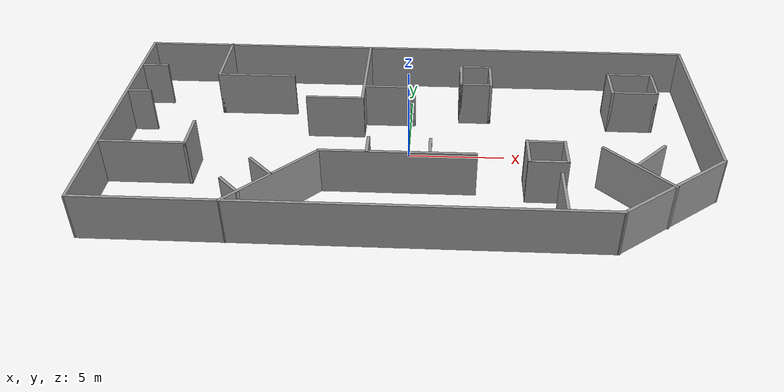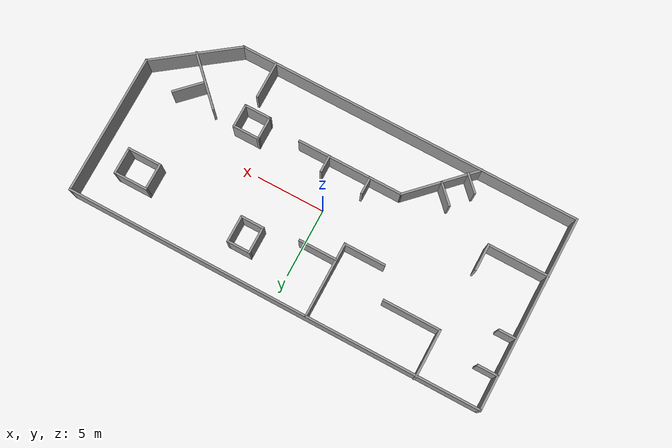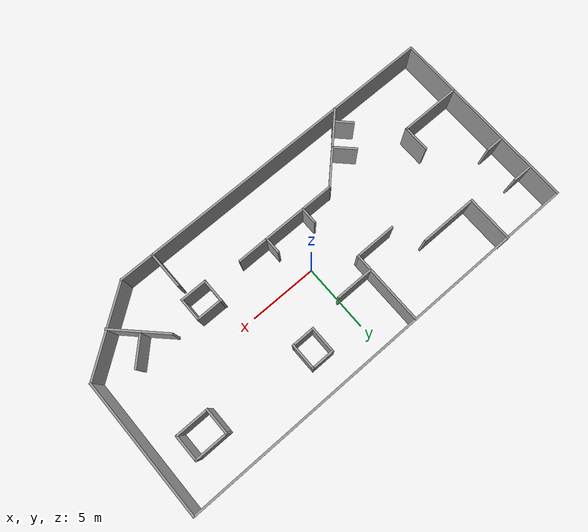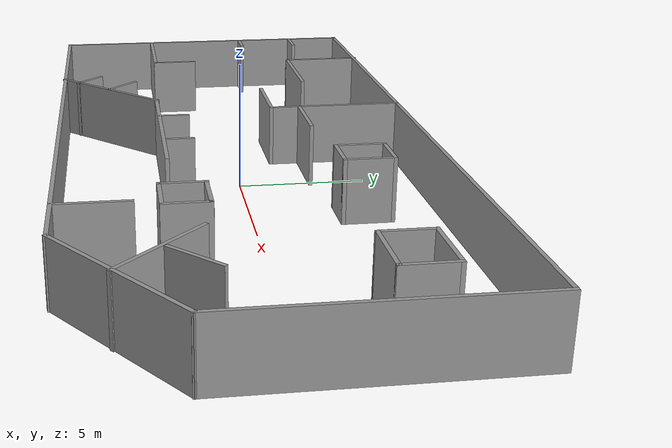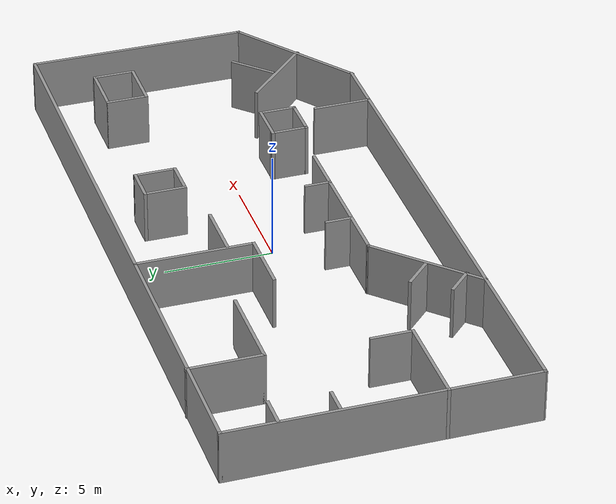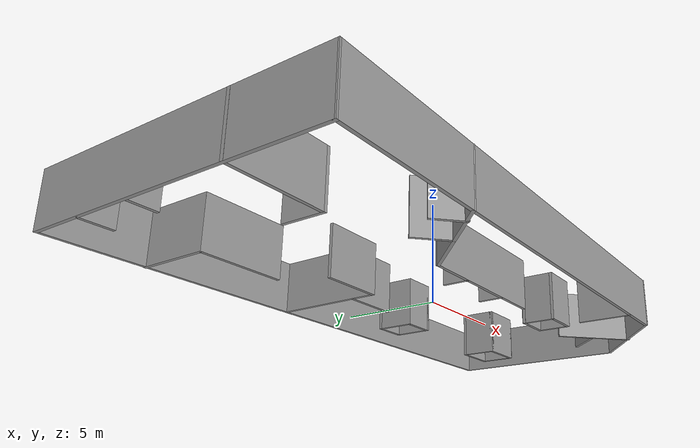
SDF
<?xml version='1.0'?>
<sdf version='1.7'>
  <model name='environment2'>
    <link name='Wall_1'>
      <pose>-0.014934 7.01964 0 0 -0 0</pose>
      <self_collide>0</self_collide>
      <enable_wind>0</enable_wind>
      <kinematic>0</kinematic>
      <visual name='Wall_1_Visual'>
        <pose>0 0 1.25 0 -0 0</pose>
        <geometry>
          <box>
            <size>30.5 0.15 2.5</size>
          </box>
        </geometry>
        <material>
          <script>
            <uri>file://media/materials/scripts/gazebo.material</uri>
            <name>Gazebo/Grey</name>
          </script>
          <ambient>1 1 1 1</ambient>
          <shader type='pixel'/>
        </material>
        <meta>
          <layer>0</layer>
        </meta>
        <transparency>0</transparency>
        <cast_shadows>1</cast_shadows>
      </visual>
      <collision name='Wall_1_Collision'>
        <laser_retro>0</laser_retro>
        <max_contacts>10</max_contacts>
        <pose>0 0 1.25 0 -0 0</pose>
        <geometry>
          <box>
            <size>30.5 0.15 2.5</size>
          </box>
        </geometry>
        <surface>
          <friction>
            <ode>
              <mu>1</mu>
              <mu2>1</mu2>
              <fdir1>0 0 0</fdir1>
              <slip1>0</slip1>
              <slip2>0</slip2>
            </ode>
            <torsional>
              <coefficient>1</coefficient>
              <patch_radius>0</patch_radius>
              <surface_radius>0</surface_radius>
              <use_patch_radius>1</use_patch_radius>
              <ode>
                <slip>0</slip>
              </ode>
            </torsional>
          </friction>
          <bounce>
            <restitution_coefficient>0</restitution_coefficient>
            <threshold>1e+06</threshold>
          </bounce>
          <contact>
            <collide_without_contact>0</collide_without_contact>
            <collide_without_contact_bitmask>1</collide_without_contact_bitmask>
            <collide_bitmask>1</collide_bitmask>
            <ode>
              <soft_cfm>0</soft_cfm>
              <soft_erp>0.2</soft_erp>
              <kp>1e+13</kp>
              <kd>1</kd>
              <max_vel>0.01</max_vel>
              <min_depth>0</min_depth>
            </ode>
            <bullet>
              <split_impulse>1</split_impulse>
              <split_impulse_penetration_threshold>-0.01</split_impulse_penetration_threshold>
              <soft_cfm>0</soft_cfm>
              <soft_erp>0.2</soft_erp>
              <kp>1e+13</kp>
              <kd>1</kd>
            </bullet>
          </contact>
        </surface>
      </collision>
    </link>
    <link name='Wall_10'>
      <pose>-15.1867 0.007115 0 0 0 -1.57033</pose>
      <self_collide>0</self_collide>
      <enable_wind>0</enable_wind>
      <kinematic>0</kinematic>
      <visual name='Wall_10_Visual'>
        <pose>0 0 1.25 0 -0 0</pose>
        <geometry>
          <box>
            <size>14.1751 0.15 2.5</size>
          </box>
        </geometry>
        <material>
          <script>
            <uri>file://media/materials/scripts/gazebo.material</uri>
            <name>Gazebo/Grey</name>
          </script>
          <ambient>1 1 1 1</ambient>
          <shader type='pixel'/>
        </material>
        <meta>
          <layer>0</layer>
        </meta>
        <transparency>0</transparency>
        <cast_shadows>1</cast_shadows>
      </visual>
      <collision name='Wall_10_Collision'>
        <laser_retro>0</laser_retro>
        <max_contacts>10</max_contacts>
        <pose>0 0 1.25 0 -0 0</pose>
        <geometry>
          <box>
            <size>14.1751 0.15 2.5</size>
          </box>
        </geometry>
        <surface>
          <friction>
            <ode>
              <mu>1</mu>
              <mu2>1</mu2>
              <fdir1>0 0 0</fdir1>
              <slip1>0</slip1>
              <slip2>0</slip2>
            </ode>
            <torsional>
              <coefficient>1</coefficient>
              <patch_radius>0</patch_radius>
              <surface_radius>0</surface_radius>
              <use_patch_radius>1</use_patch_radius>
              <ode>
                <slip>0</slip>
              </ode>
            </torsional>
          </friction>
          <bounce>
            <restitution_coefficient>0</restitution_coefficient>
            <threshold>1e+06</threshold>
          </bounce>
          <contact>
            <collide_without_contact>0</collide_without_contact>
            <collide_without_contact_bitmask>1</collide_without_contact_bitmask>
            <collide_bitmask>1</collide_bitmask>
            <ode>
              <soft_cfm>0</soft_cfm>
              <soft_erp>0.2</soft_erp>
              <kp>1e+13</kp>
              <kd>1</kd>
              <max_vel>0.01</max_vel>
              <min_depth>0</min_depth>
            </ode>
            <bullet>
              <split_impulse>1</split_impulse>
              <split_impulse_penetration_threshold>-0.01</split_impulse_penetration_threshold>
              <soft_cfm>0</soft_cfm>
              <soft_erp>0.2</soft_erp>
              <kp>1e+13</kp>
              <kd>1</kd>
            </bullet>
          </contact>
        </surface>
      </collision>
    </link>
    <link name='Wall_13'>
      <pose>-10.5995 5.38344 0 0 0 -1.5708</pose>
      <self_collide>0</self_collide>
      <enable_wind>0</enable_wind>
      <kinematic>0</kinematic>
      <visual name='Wall_13_Visual'>
        <pose>0 0 1.25 0 -0 0</pose>
        <geometry>
          <box>
            <size>3.5 0.15 2.5</size>
          </box>
        </geometry>
        <material>
          <script>
            <uri>file://media/materials/scripts/gazebo.material</uri>
            <name>Gazebo/Grey</name>
          </script>
          <ambient>1 1 1 1</ambient>
          <shader type='pixel'/>
        </material>
        <meta>
          <layer>0</layer>
        </meta>
        <transparency>0</transparency>
        <cast_shadows>1</cast_shadows>
      </visual>
      <collision name='Wall_13_Collision'>
        <laser_retro>0</laser_retro>
        <max_contacts>10</max_contacts>
        <pose>0 0 1.25 0 -0 0</pose>
        <geometry>
          <box>
            <size>3.5 0.15 2.5</size>
          </box>
        </geometry>
        <surface>
          <friction>
            <ode>
              <mu>1</mu>
              <mu2>1</mu2>
              <fdir1>0 0 0</fdir1>
              <slip1>0</slip1>
              <slip2>0</slip2>
            </ode>
            <torsional>
              <coefficient>1</coefficient>
              <patch_radius>0</patch_radius>
              <surface_radius>0</surface_radius>
              <use_patch_radius>1</use_patch_radius>
              <ode>
                <slip>0</slip>
              </ode>
            </torsional>
          </friction>
          <bounce>
            <restitution_coefficient>0</restitution_coefficient>
            <threshold>1e+06</threshold>
          </bounce>
          <contact>
            <collide_without_contact>0</collide_without_contact>
            <collide_without_contact_bitmask>1</collide_without_contact_bitmask>
            <collide_bitmask>1</collide_bitmask>
            <ode>
              <soft_cfm>0</soft_cfm>
              <soft_erp>0.2</soft_erp>
              <kp>1e+13</kp>
              <kd>1</kd>
              <max_vel>0.01</max_vel>
              <min_depth>0</min_depth>
            </ode>
            <bullet>
              <split_impulse>1</split_impulse>
              <split_impulse_penetration_threshold>-0.01</split_impulse_penetration_threshold>
              <soft_cfm>0</soft_cfm>
              <soft_erp>0.2</soft_erp>
              <kp>1e+13</kp>
              <kd>1</kd>
            </bullet>
          </contact>
        </surface>
      </collision>
    </link>
    <link name='Wall_14'>
      <pose>-8.5495 3.70844 0 0 -0 0</pose>
      <self_collide>0</self_collide>
      <enable_wind>0</enable_wind>
      <kinematic>0</kinematic>
      <visual name='Wall_14_Visual'>
        <pose>0 0 1.25 0 -0 0</pose>
        <geometry>
          <box>
            <size>4.25 0.15 2.5</size>
          </box>
        </geometry>
        <material>
          <script>
            <uri>file://media/materials/scripts/gazebo.material</uri>
            <name>Gazebo/Grey</name>
          </script>
          <ambient>1 1 1 1</ambient>
          <shader type='pixel'/>
        </material>
        <meta>
          <layer>0</layer>
        </meta>
        <transparency>0</transparency>
        <cast_shadows>1</cast_shadows>
      </visual>
      <collision name='Wall_14_Collision'>
        <laser_retro>0</laser_retro>
        <max_contacts>10</max_contacts>
        <pose>0 0 1.25 0 -0 0</pose>
        <geometry>
          <box>
            <size>4.25 0.15 2.5</size>
          </box>
        </geometry>
        <surface>
          <friction>
            <ode>
              <mu>1</mu>
              <mu2>1</mu2>
              <fdir1>0 0 0</fdir1>
              <slip1>0</slip1>
              <slip2>0</slip2>
            </ode>
            <torsional>
              <coefficient>1</coefficient>
              <patch_radius>0</patch_radius>
              <surface_radius>0</surface_radius>
              <use_patch_radius>1</use_patch_radius>
              <ode>
                <slip>0</slip>
              </ode>
            </torsional>
          </friction>
          <bounce>
            <restitution_coefficient>0</restitution_coefficient>
            <threshold>1e+06</threshold>
          </bounce>
          <contact>
            <collide_without_contact>0</collide_without_contact>
            <collide_without_contact_bitmask>1</collide_without_contact_bitmask>
            <collide_bitmask>1</collide_bitmask>
            <ode>
              <soft_cfm>0</soft_cfm>
              <soft_erp>0.2</soft_erp>
              <kp>1e+13</kp>
              <kd>1</kd>
              <max_vel>0.01</max_vel>
              <min_depth>0</min_depth>
            </ode>
            <bullet>
              <split_impulse>1</split_impulse>
              <split_impulse_penetration_threshold>-0.01</split_impulse_penetration_threshold>
              <soft_cfm>0</soft_cfm>
              <soft_erp>0.2</soft_erp>
              <kp>1e+13</kp>
              <kd>1</kd>
            </bullet>
          </contact>
        </surface>
      </collision>
    </link>
    <link name='Wall_16'>
      <pose>-2.52368 4.32226 0 0 0 -1.5708</pose>
      <self_collide>0</self_collide>
      <enable_wind>0</enable_wind>
      <kinematic>0</kinematic>
      <visual name='Wall_16_Visual'>
        <pose>0 0 1.25 0 -0 0</pose>
        <geometry>
          <box>
            <size>5.5 0.15 2.5</size>
          </box>
        </geometry>
        <material>
          <script>
            <uri>file://media/materials/scripts/gazebo.material</uri>
            <name>Gazebo/Grey</name>
          </script>
          <ambient>1 1 1 1</ambient>
          <shader type='pixel'/>
        </material>
        <meta>
          <layer>0</layer>
        </meta>
        <transparency>0</transparency>
        <cast_shadows>1</cast_shadows>
      </visual>
      <collision name='Wall_16_Collision'>
        <laser_retro>0</laser_retro>
        <max_contacts>10</max_contacts>
        <pose>0 0 1.25 0 -0 0</pose>
        <geometry>
          <box>
            <size>5.5 0.15 2.5</size>
          </box>
        </geometry>
        <surface>
          <friction>
            <ode>
              <mu>1</mu>
              <mu2>1</mu2>
              <fdir1>0 0 0</fdir1>
              <slip1>0</slip1>
              <slip2>0</slip2>
            </ode>
            <torsional>
              <coefficient>1</coefficient>
              <patch_radius>0</patch_radius>
              <surface_radius>0</surface_radius>
              <use_patch_radius>1</use_patch_radius>
              <ode>
                <slip>0</slip>
              </ode>
            </torsional>
          </friction>
          <bounce>
            <restitution_coefficient>0</restitution_coefficient>
            <threshold>1e+06</threshold>
          </bounce>
          <contact>
            <collide_without_contact>0</collide_without_contact>
            <collide_without_contact_bitmask>1</collide_without_contact_bitmask>
            <collide_bitmask>1</collide_bitmask>
            <ode>
              <soft_cfm>0</soft_cfm>
              <soft_erp>0.2</soft_erp>
              <kp>1e+13</kp>
              <kd>1</kd>
              <max_vel>0.01</max_vel>
              <min_depth>0</min_depth>
            </ode>
            <bullet>
              <split_impulse>1</split_impulse>
              <split_impulse_penetration_threshold>-0.01</split_impulse_penetration_threshold>
              <soft_cfm>0</soft_cfm>
              <soft_erp>0.2</soft_erp>
              <kp>1e+13</kp>
              <kd>1</kd>
            </bullet>
          </contact>
        </surface>
      </collision>
    </link>
    <link name='Wall_17'>
      <pose>-3.97927 1.64726 0 0 -0 3.14159</pose>
      <self_collide>0</self_collide>
      <enable_wind>0</enable_wind>
      <kinematic>0</kinematic>
      <visual name='Wall_17_Visual'>
        <pose>0 0 1.25 0 -0 0</pose>
        <geometry>
          <box>
            <size>3.06118 0.15 2.5</size>
          </box>
        </geometry>
        <material>
          <script>
            <uri>file://media/materials/scripts/gazebo.material</uri>
            <name>Gazebo/Grey</name>
          </script>
          <ambient>1 1 1 1</ambient>
          <shader type='pixel'/>
        </material>
        <meta>
          <layer>0</layer>
        </meta>
        <transparency>0</transparency>
        <cast_shadows>1</cast_shadows>
      </visual>
      <collision name='Wall_17_Collision'>
        <laser_retro>0</laser_retro>
        <max_contacts>10</max_contacts>
        <pose>0 0 1.25 0 -0 0</pose>
        <geometry>
          <box>
            <size>3.06118 0.15 2.5</size>
          </box>
        </geometry>
        <surface>
          <friction>
            <ode>
              <mu>1</mu>
              <mu2>1</mu2>
              <fdir1>0 0 0</fdir1>
              <slip1>0</slip1>
              <slip2>0</slip2>
            </ode>
            <torsional>
              <coefficient>1</coefficient>
              <patch_radius>0</patch_radius>
              <surface_radius>0</surface_radius>
              <use_patch_radius>1</use_patch_radius>
              <ode>
                <slip>0</slip>
              </ode>
            </torsional>
          </friction>
          <bounce>
            <restitution_coefficient>0</restitution_coefficient>
            <threshold>1e+06</threshold>
          </bounce>
          <contact>
            <collide_without_contact>0</collide_without_contact>
            <collide_without_contact_bitmask>1</collide_without_contact_bitmask>
            <collide_bitmask>1</collide_bitmask>
            <ode>
              <soft_cfm>0</soft_cfm>
              <soft_erp>0.2</soft_erp>
              <kp>1e+13</kp>
              <kd>1</kd>
              <max_vel>0.01</max_vel>
              <min_depth>0</min_depth>
            </ode>
            <bullet>
              <split_impulse>1</split_impulse>
              <split_impulse_penetration_threshold>-0.01</split_impulse_penetration_threshold>
              <soft_cfm>0</soft_cfm>
              <soft_erp>0.2</soft_erp>
              <kp>1e+13</kp>
              <kd>1</kd>
            </bullet>
          </contact>
        </surface>
      </collision>
    </link>
    <link name='Wall_2'>
      <pose>15.1601 1.96964 0 0 0 -1.5708</pose>
      <self_collide>0</self_collide>
      <enable_wind>0</enable_wind>
      <kinematic>0</kinematic>
      <visual name='Wall_2_Visual'>
        <pose>0 0 1.25 0 -0 0</pose>
        <geometry>
          <box>
            <size>10.25 0.15 2.5</size>
          </box>
        </geometry>
        <material>
          <script>
            <uri>file://media/materials/scripts/gazebo.material</uri>
            <name>Gazebo/Grey</name>
          </script>
          <ambient>1 1 1 1</ambient>
          <shader type='pixel'/>
        </material>
        <meta>
          <layer>0</layer>
        </meta>
        <transparency>0</transparency>
        <cast_shadows>1</cast_shadows>
      </visual>
      <collision name='Wall_2_Collision'>
        <laser_retro>0</laser_retro>
        <max_contacts>10</max_contacts>
        <pose>0 0 1.25 0 -0 0</pose>
        <geometry>
          <box>
            <size>10.25 0.15 2.5</size>
          </box>
        </geometry>
        <surface>
          <friction>
            <ode>
              <mu>1</mu>
              <mu2>1</mu2>
              <fdir1>0 0 0</fdir1>
              <slip1>0</slip1>
              <slip2>0</slip2>
            </ode>
            <torsional>
              <coefficient>1</coefficient>
              <patch_radius>0</patch_radius>
              <surface_radius>0</surface_radius>
              <use_patch_radius>1</use_patch_radius>
              <ode>
                <slip>0</slip>
              </ode>
            </torsional>
          </friction>
          <bounce>
            <restitution_coefficient>0</restitution_coefficient>
            <threshold>1e+06</threshold>
          </bounce>
          <contact>
            <collide_without_contact>0</collide_without_contact>
            <collide_without_contact_bitmask>1</collide_without_contact_bitmask>
            <collide_bitmask>1</collide_bitmask>
            <ode>
              <soft_cfm>0</soft_cfm>
              <soft_erp>0.2</soft_erp>
              <kp>1e+13</kp>
              <kd>1</kd>
              <max_vel>0.01</max_vel>
              <min_depth>0</min_depth>
            </ode>
            <bullet>
              <split_impulse>1</split_impulse>
              <split_impulse_penetration_threshold>-0.01</split_impulse_penetration_threshold>
              <soft_cfm>0</soft_cfm>
              <soft_erp>0.2</soft_erp>
              <kp>1e+13</kp>
              <kd>1</kd>
            </bullet>
          </contact>
        </surface>
      </collision>
    </link>
    <link name='Wall_20'>
      <pose>-13.013 -2.76102 0 0 -0 0</pose>
      <self_collide>0</self_collide>
      <enable_wind>0</enable_wind>
      <kinematic>0</kinematic>
      <visual name='Wall_20_Visual'>
        <pose>0 0 1.25 0 -0 0</pose>
        <geometry>
          <box>
            <size>4.5 0.15 2.5</size>
          </box>
        </geometry>
        <material>
          <script>
            <uri>file://media/materials/scripts/gazebo.material</uri>
            <name>Gazebo/Grey</name>
          </script>
          <ambient>1 1 1 1</ambient>
          <shader type='pixel'/>
        </material>
        <meta>
          <layer>0</layer>
        </meta>
        <transparency>0</transparency>
        <cast_shadows>1</cast_shadows>
      </visual>
      <collision name='Wall_20_Collision'>
        <laser_retro>0</laser_retro>
        <max_contacts>10</max_contacts>
        <pose>0 0 1.25 0 -0 0</pose>
        <geometry>
          <box>
            <size>4.5 0.15 2.5</size>
          </box>
        </geometry>
        <surface>
          <friction>
            <ode>
              <mu>1</mu>
              <mu2>1</mu2>
              <fdir1>0 0 0</fdir1>
              <slip1>0</slip1>
              <slip2>0</slip2>
            </ode>
            <torsional>
              <coefficient>1</coefficient>
              <patch_radius>0</patch_radius>
              <surface_radius>0</surface_radius>
              <use_patch_radius>1</use_patch_radius>
              <ode>
                <slip>0</slip>
              </ode>
            </torsional>
          </friction>
          <bounce>
            <restitution_coefficient>0</restitution_coefficient>
            <threshold>1e+06</threshold>
          </bounce>
          <contact>
            <collide_without_contact>0</collide_without_contact>
            <collide_without_contact_bitmask>1</collide_without_contact_bitmask>
            <collide_bitmask>1</collide_bitmask>
            <ode>
              <soft_cfm>0</soft_cfm>
              <soft_erp>0.2</soft_erp>
              <kp>1e+13</kp>
              <kd>1</kd>
              <max_vel>0.01</max_vel>
              <min_depth>0</min_depth>
            </ode>
            <bullet>
              <split_impulse>1</split_impulse>
              <split_impulse_penetration_threshold>-0.01</split_impulse_penetration_threshold>
              <soft_cfm>0</soft_cfm>
              <soft_erp>0.2</soft_erp>
              <kp>1e+13</kp>
              <kd>1</kd>
            </bullet>
          </contact>
        </surface>
      </collision>
    </link>
    <link name='Wall_21'>
      <pose>-10.838 -1.83602 0 0 -0 1.5708</pose>
      <self_collide>0</self_collide>
      <enable_wind>0</enable_wind>
      <kinematic>0</kinematic>
      <visual name='Wall_21_Visual'>
        <pose>0 0 1.25 0 -0 0</pose>
        <geometry>
          <box>
            <size>2 0.15 2.5</size>
          </box>
        </geometry>
        <material>
          <script>
            <uri>file://media/materials/scripts/gazebo.material</uri>
            <name>Gazebo/Grey</name>
          </script>
          <ambient>1 1 1 1</ambient>
          <shader type='pixel'/>
        </material>
        <meta>
          <layer>0</layer>
        </meta>
        <transparency>0</transparency>
        <cast_shadows>1</cast_shadows>
      </visual>
      <collision name='Wall_21_Collision'>
        <laser_retro>0</laser_retro>
        <max_contacts>10</max_contacts>
        <pose>0 0 1.25 0 -0 0</pose>
        <geometry>
          <box>
            <size>2 0.15 2.5</size>
          </box>
        </geometry>
        <surface>
          <friction>
            <ode>
              <mu>1</mu>
              <mu2>1</mu2>
              <fdir1>0 0 0</fdir1>
              <slip1>0</slip1>
              <slip2>0</slip2>
            </ode>
            <torsional>
              <coefficient>1</coefficient>
              <patch_radius>0</patch_radius>
              <surface_radius>0</surface_radius>
              <use_patch_radius>1</use_patch_radius>
              <ode>
                <slip>0</slip>
              </ode>
            </torsional>
          </friction>
          <bounce>
            <restitution_coefficient>0</restitution_coefficient>
            <threshold>1e+06</threshold>
          </bounce>
          <contact>
            <collide_without_contact>0</collide_without_contact>
            <collide_without_contact_bitmask>1</collide_without_contact_bitmask>
            <collide_bitmask>1</collide_bitmask>
            <ode>
              <soft_cfm>0</soft_cfm>
              <soft_erp>0.2</soft_erp>
              <kp>1e+13</kp>
              <kd>1</kd>
              <max_vel>0.01</max_vel>
              <min_depth>0</min_depth>
            </ode>
            <bullet>
              <split_impulse>1</split_impulse>
              <split_impulse_penetration_threshold>-0.01</split_impulse_penetration_threshold>
              <soft_cfm>0</soft_cfm>
              <soft_erp>0.2</soft_erp>
              <kp>1e+13</kp>
              <kd>1</kd>
            </bullet>
          </contact>
        </surface>
      </collision>
    </link>
    <link name='Wall_23'>
      <pose>-6.20298 -5.03317 0 0 -0 0.785398</pose>
      <self_collide>0</self_collide>
      <enable_wind>0</enable_wind>
      <kinematic>0</kinematic>
      <visual name='Wall_23_Visual'>
        <pose>0 0 1.25 0 -0 0</pose>
        <geometry>
          <box>
            <size>5.75 0.15 2.5</size>
          </box>
        </geometry>
        <material>
          <script>
            <uri>file://media/materials/scripts/gazebo.material</uri>
            <name>Gazebo/Grey</name>
          </script>
          <ambient>1 1 1 1</ambient>
          <shader type='pixel'/>
        </material>
        <meta>
          <layer>0</layer>
        </meta>
        <transparency>0</transparency>
        <cast_shadows>1</cast_shadows>
      </visual>
      <collision name='Wall_23_Collision'>
        <laser_retro>0</laser_retro>
        <max_contacts>10</max_contacts>
        <pose>0 0 1.25 0 -0 0</pose>
        <geometry>
          <box>
            <size>5.75 0.15 2.5</size>
          </box>
        </geometry>
        <surface>
          <friction>
            <ode>
              <mu>1</mu>
              <mu2>1</mu2>
              <fdir1>0 0 0</fdir1>
              <slip1>0</slip1>
              <slip2>0</slip2>
            </ode>
            <torsional>
              <coefficient>1</coefficient>
              <patch_radius>0</patch_radius>
              <surface_radius>0</surface_radius>
              <use_patch_radius>1</use_patch_radius>
              <ode>
                <slip>0</slip>
              </ode>
            </torsional>
          </friction>
          <bounce>
            <restitution_coefficient>0</restitution_coefficient>
            <threshold>1e+06</threshold>
          </bounce>
          <contact>
            <collide_without_contact>0</collide_without_contact>
            <collide_without_contact_bitmask>1</collide_without_contact_bitmask>
            <collide_bitmask>1</collide_bitmask>
            <ode>
              <soft_cfm>0</soft_cfm>
              <soft_erp>0.2</soft_erp>
              <kp>1e+13</kp>
              <kd>1</kd>
              <max_vel>0.01</max_vel>
              <min_depth>0</min_depth>
            </ode>
            <bullet>
              <split_impulse>1</split_impulse>
              <split_impulse_penetration_threshold>-0.01</split_impulse_penetration_threshold>
              <soft_cfm>0</soft_cfm>
              <soft_erp>0.2</soft_erp>
              <kp>1e+13</kp>
              <kd>1</kd>
            </bullet>
          </contact>
        </surface>
      </collision>
    </link>
    <link name='Wall_25'>
      <pose>-0.423078 -3.05327 0 0 -0 0</pose>
      <self_collide>0</self_collide>
      <enable_wind>0</enable_wind>
      <kinematic>0</kinematic>
      <visual name='Wall_25_Visual'>
        <pose>0 0 1.25 0 -0 0</pose>
        <geometry>
          <box>
            <size>7.75 0.15 2.5</size>
          </box>
        </geometry>
        <material>
          <script>
            <uri>file://media/materials/scripts/gazebo.material</uri>
            <name>Gazebo/Grey</name>
          </script>
          <ambient>1 1 1 1</ambient>
          <shader type='pixel'/>
        </material>
        <meta>
          <layer>0</layer>
        </meta>
        <transparency>0</transparency>
        <cast_shadows>1</cast_shadows>
      </visual>
      <collision name='Wall_25_Collision'>
        <laser_retro>0</laser_retro>
        <max_contacts>10</max_contacts>
        <pose>0 0 1.25 0 -0 0</pose>
        <geometry>
          <box>
            <size>7.75 0.15 2.5</size>
          </box>
        </geometry>
        <surface>
          <friction>
            <ode>
              <mu>1</mu>
              <mu2>1</mu2>
              <fdir1>0 0 0</fdir1>
              <slip1>0</slip1>
              <slip2>0</slip2>
            </ode>
            <torsional>
              <coefficient>1</coefficient>
              <patch_radius>0</patch_radius>
              <surface_radius>0</surface_radius>
              <use_patch_radius>1</use_patch_radius>
              <ode>
                <slip>0</slip>
              </ode>
            </torsional>
          </friction>
          <bounce>
            <restitution_coefficient>0</restitution_coefficient>
            <threshold>1e+06</threshold>
          </bounce>
          <contact>
            <collide_without_contact>0</collide_without_contact>
            <collide_without_contact_bitmask>1</collide_without_contact_bitmask>
            <collide_bitmask>1</collide_bitmask>
            <ode>
              <soft_cfm>0</soft_cfm>
              <soft_erp>0.2</soft_erp>
              <kp>1e+13</kp>
              <kd>1</kd>
              <max_vel>0.01</max_vel>
              <min_depth>0</min_depth>
            </ode>
            <bullet>
              <split_impulse>1</split_impulse>
              <split_impulse_penetration_threshold>-0.01</split_impulse_penetration_threshold>
              <soft_cfm>0</soft_cfm>
              <soft_erp>0.2</soft_erp>
              <kp>1e+13</kp>
              <kd>1</kd>
            </bullet>
          </contact>
        </surface>
      </collision>
    </link>
    <link name='Wall_27'>
      <pose>2.70725 4.17567 0 0 0 -1.5708</pose>
      <self_collide>0</self_collide>
      <enable_wind>0</enable_wind>
      <kinematic>0</kinematic>
      <visual name='Wall_27_Visual'>
        <pose>0 0 1.25 0 -0 0</pose>
        <geometry>
          <box>
            <size>2 0.15 2.5</size>
          </box>
        </geometry>
        <material>
          <script>
            <uri>file://media/materials/scripts/gazebo.material</uri>
            <name>Gazebo/Grey</name>
          </script>
          <ambient>1 1 1 1</ambient>
          <shader type='pixel'/>
        </material>
        <meta>
          <layer>0</layer>
        </meta>
        <transparency>0</transparency>
        <cast_shadows>1</cast_shadows>
      </visual>
      <collision name='Wall_27_Collision'>
        <laser_retro>0</laser_retro>
        <max_contacts>10</max_contacts>
        <pose>0 0 1.25 0 -0 0</pose>
        <geometry>
          <box>
            <size>2 0.15 2.5</size>
          </box>
        </geometry>
        <surface>
          <friction>
            <ode>
              <mu>1</mu>
              <mu2>1</mu2>
              <fdir1>0 0 0</fdir1>
              <slip1>0</slip1>
              <slip2>0</slip2>
            </ode>
            <torsional>
              <coefficient>1</coefficient>
              <patch_radius>0</patch_radius>
              <surface_radius>0</surface_radius>
              <use_patch_radius>1</use_patch_radius>
              <ode>
                <slip>0</slip>
              </ode>
            </torsional>
          </friction>
          <bounce>
            <restitution_coefficient>0</restitution_coefficient>
            <threshold>1e+06</threshold>
          </bounce>
          <contact>
            <collide_without_contact>0</collide_without_contact>
            <collide_without_contact_bitmask>1</collide_without_contact_bitmask>
            <collide_bitmask>1</collide_bitmask>
            <ode>
              <soft_cfm>0</soft_cfm>
              <soft_erp>0.2</soft_erp>
              <kp>1e+13</kp>
              <kd>1</kd>
              <max_vel>0.01</max_vel>
              <min_depth>0</min_depth>
            </ode>
            <bullet>
              <split_impulse>1</split_impulse>
              <split_impulse_penetration_threshold>-0.01</split_impulse_penetration_threshold>
              <soft_cfm>0</soft_cfm>
              <soft_erp>0.2</soft_erp>
              <kp>1e+13</kp>
              <kd>1</kd>
            </bullet>
          </contact>
        </surface>
      </collision>
    </link>
    <link name='Wall_28'>
      <pose>3.50725 3.25067 0 0 -0 0</pose>
      <self_collide>0</self_collide>
      <enable_wind>0</enable_wind>
      <kinematic>0</kinematic>
      <visual name='Wall_28_Visual'>
        <pose>0 0 1.25 0 -0 0</pose>
        <geometry>
          <box>
            <size>1.75 0.15 2.5</size>
          </box>
        </geometry>
        <material>
          <script>
            <uri>file://media/materials/scripts/gazebo.material</uri>
            <name>Gazebo/Grey</name>
          </script>
          <ambient>1 1 1 1</ambient>
          <shader type='pixel'/>
        </material>
        <meta>
          <layer>0</layer>
        </meta>
        <transparency>0</transparency>
        <cast_shadows>1</cast_shadows>
      </visual>
      <collision name='Wall_28_Collision'>
        <laser_retro>0</laser_retro>
        <max_contacts>10</max_contacts>
        <pose>0 0 1.25 0 -0 0</pose>
        <geometry>
          <box>
            <size>1.75 0.15 2.5</size>
          </box>
        </geometry>
        <surface>
          <friction>
            <ode>
              <mu>1</mu>
              <mu2>1</mu2>
              <fdir1>0 0 0</fdir1>
              <slip1>0</slip1>
              <slip2>0</slip2>
            </ode>
            <torsional>
              <coefficient>1</coefficient>
              <patch_radius>0</patch_radius>
              <surface_radius>0</surface_radius>
              <use_patch_radius>1</use_patch_radius>
              <ode>
                <slip>0</slip>
              </ode>
            </torsional>
          </friction>
          <bounce>
            <restitution_coefficient>0</restitution_coefficient>
            <threshold>1e+06</threshold>
          </bounce>
          <contact>
            <collide_without_contact>0</collide_without_contact>
            <collide_without_contact_bitmask>1</collide_without_contact_bitmask>
            <collide_bitmask>1</collide_bitmask>
            <ode>
              <soft_cfm>0</soft_cfm>
              <soft_erp>0.2</soft_erp>
              <kp>1e+13</kp>
              <kd>1</kd>
              <max_vel>0.01</max_vel>
              <min_depth>0</min_depth>
            </ode>
            <bullet>
              <split_impulse>1</split_impulse>
              <split_impulse_penetration_threshold>-0.01</split_impulse_penetration_threshold>
              <soft_cfm>0</soft_cfm>
              <soft_erp>0.2</soft_erp>
              <kp>1e+13</kp>
              <kd>1</kd>
            </bullet>
          </contact>
        </surface>
      </collision>
    </link>
    <link name='Wall_29'>
      <pose>4.30724 4.17567 0 0 -0 1.5708</pose>
      <self_collide>0</self_collide>
      <enable_wind>0</enable_wind>
      <kinematic>0</kinematic>
      <visual name='Wall_29_Visual'>
        <pose>0 0 1.25 0 -0 0</pose>
        <geometry>
          <box>
            <size>2 0.15 2.5</size>
          </box>
        </geometry>
        <material>
          <script>
            <uri>file://media/materials/scripts/gazebo.material</uri>
            <name>Gazebo/Grey</name>
          </script>
          <ambient>1 1 1 1</ambient>
          <shader type='pixel'/>
        </material>
        <meta>
          <layer>0</layer>
        </meta>
        <transparency>0</transparency>
        <cast_shadows>1</cast_shadows>
      </visual>
      <collision name='Wall_29_Collision'>
        <laser_retro>0</laser_retro>
        <max_contacts>10</max_contacts>
        <pose>0 0 1.25 0 -0 0</pose>
        <geometry>
          <box>
            <size>2 0.15 2.5</size>
          </box>
        </geometry>
        <surface>
          <friction>
            <ode>
              <mu>1</mu>
              <mu2>1</mu2>
              <fdir1>0 0 0</fdir1>
              <slip1>0</slip1>
              <slip2>0</slip2>
            </ode>
            <torsional>
              <coefficient>1</coefficient>
              <patch_radius>0</patch_radius>
              <surface_radius>0</surface_radius>
              <use_patch_radius>1</use_patch_radius>
              <ode>
                <slip>0</slip>
              </ode>
            </torsional>
          </friction>
          <bounce>
            <restitution_coefficient>0</restitution_coefficient>
            <threshold>1e+06</threshold>
          </bounce>
          <contact>
            <collide_without_contact>0</collide_without_contact>
            <collide_without_contact_bitmask>1</collide_without_contact_bitmask>
            <collide_bitmask>1</collide_bitmask>
            <ode>
              <soft_cfm>0</soft_cfm>
              <soft_erp>0.2</soft_erp>
              <kp>1e+13</kp>
              <kd>1</kd>
              <max_vel>0.01</max_vel>
              <min_depth>0</min_depth>
            </ode>
            <bullet>
              <split_impulse>1</split_impulse>
              <split_impulse_penetration_threshold>-0.01</split_impulse_penetration_threshold>
              <soft_cfm>0</soft_cfm>
              <soft_erp>0.2</soft_erp>
              <kp>1e+13</kp>
              <kd>1</kd>
            </bullet>
          </contact>
        </surface>
      </collision>
    </link>
    <link name='Wall_3'>
      <pose>12.4921 -5.05445 0 0 0 -2.50458</pose>
      <self_collide>0</self_collide>
      <enable_wind>0</enable_wind>
      <kinematic>0</kinematic>
      <visual name='Wall_3_Visual'>
        <pose>0 0 1.25 0 -0 0</pose>
        <geometry>
          <box>
            <size>6.78786 0.15 2.5</size>
          </box>
        </geometry>
        <material>
          <script>
            <uri>file://media/materials/scripts/gazebo.material</uri>
            <name>Gazebo/Grey</name>
          </script>
          <ambient>1 1 1 1</ambient>
          <shader type='pixel'/>
        </material>
        <meta>
          <layer>0</layer>
        </meta>
        <transparency>0</transparency>
        <cast_shadows>1</cast_shadows>
      </visual>
      <collision name='Wall_3_Collision'>
        <laser_retro>0</laser_retro>
        <max_contacts>10</max_contacts>
        <pose>0 0 1.25 0 -0 0</pose>
        <geometry>
          <box>
            <size>6.78786 0.15 2.5</size>
          </box>
        </geometry>
        <surface>
          <friction>
            <ode>
              <mu>1</mu>
              <mu2>1</mu2>
              <fdir1>0 0 0</fdir1>
              <slip1>0</slip1>
              <slip2>0</slip2>
            </ode>
            <torsional>
              <coefficient>1</coefficient>
              <patch_radius>0</patch_radius>
              <surface_radius>0</surface_radius>
              <use_patch_radius>1</use_patch_radius>
              <ode>
                <slip>0</slip>
              </ode>
            </torsional>
          </friction>
          <bounce>
            <restitution_coefficient>0</restitution_coefficient>
            <threshold>1e+06</threshold>
          </bounce>
          <contact>
            <collide_without_contact>0</collide_without_contact>
            <collide_without_contact_bitmask>1</collide_without_contact_bitmask>
            <collide_bitmask>1</collide_bitmask>
            <ode>
              <soft_cfm>0</soft_cfm>
              <soft_erp>0.2</soft_erp>
              <kp>1e+13</kp>
              <kd>1</kd>
              <max_vel>0.01</max_vel>
              <min_depth>0</min_depth>
            </ode>
            <bullet>
              <split_impulse>1</split_impulse>
              <split_impulse_penetration_threshold>-0.01</split_impulse_penetration_threshold>
              <soft_cfm>0</soft_cfm>
              <soft_erp>0.2</soft_erp>
              <kp>1e+13</kp>
              <kd>1</kd>
            </bullet>
          </contact>
        </surface>
      </collision>
    </link>
    <link name='Wall_30'>
      <pose>3.50725 5.10067 0 0 -0 3.14159</pose>
      <self_collide>0</self_collide>
      <enable_wind>0</enable_wind>
      <kinematic>0</kinematic>
      <visual name='Wall_30_Visual'>
        <pose>0 0 1.25 0 -0 0</pose>
        <geometry>
          <box>
            <size>1.75 0.15 2.5</size>
          </box>
        </geometry>
        <material>
          <script>
            <uri>file://media/materials/scripts/gazebo.material</uri>
            <name>Gazebo/Grey</name>
          </script>
          <ambient>1 1 1 1</ambient>
          <shader type='pixel'/>
        </material>
        <meta>
          <layer>0</layer>
        </meta>
        <transparency>0</transparency>
        <cast_shadows>1</cast_shadows>
      </visual>
      <collision name='Wall_30_Collision'>
        <laser_retro>0</laser_retro>
        <max_contacts>10</max_contacts>
        <pose>0 0 1.25 0 -0 0</pose>
        <geometry>
          <box>
            <size>1.75 0.15 2.5</size>
          </box>
        </geometry>
        <surface>
          <friction>
            <ode>
              <mu>1</mu>
              <mu2>1</mu2>
              <fdir1>0 0 0</fdir1>
              <slip1>0</slip1>
              <slip2>0</slip2>
            </ode>
            <torsional>
              <coefficient>1</coefficient>
              <patch_radius>0</patch_radius>
              <surface_radius>0</surface_radius>
              <use_patch_radius>1</use_patch_radius>
              <ode>
                <slip>0</slip>
              </ode>
            </torsional>
          </friction>
          <bounce>
            <restitution_coefficient>0</restitution_coefficient>
            <threshold>1e+06</threshold>
          </bounce>
          <contact>
            <collide_without_contact>0</collide_without_contact>
            <collide_without_contact_bitmask>1</collide_without_contact_bitmask>
            <collide_bitmask>1</collide_bitmask>
            <ode>
              <soft_cfm>0</soft_cfm>
              <soft_erp>0.2</soft_erp>
              <kp>1e+13</kp>
              <kd>1</kd>
              <max_vel>0.01</max_vel>
              <min_depth>0</min_depth>
            </ode>
            <bullet>
              <split_impulse>1</split_impulse>
              <split_impulse_penetration_threshold>-0.01</split_impulse_penetration_threshold>
              <soft_cfm>0</soft_cfm>
              <soft_erp>0.2</soft_erp>
              <kp>1e+13</kp>
              <kd>1</kd>
            </bullet>
          </contact>
        </surface>
      </collision>
    </link>
    <link name='Wall_32'>
      <pose>5.89662 -2.66173 0 0 0 -1.5708</pose>
      <self_collide>0</self_collide>
      <enable_wind>0</enable_wind>
      <kinematic>0</kinematic>
      <visual name='Wall_32_Visual'>
        <pose>0 0 1.25 0 -0 0</pose>
        <geometry>
          <box>
            <size>1.75 0.15 2.5</size>
          </box>
        </geometry>
        <material>
          <script>
            <uri>file://media/materials/scripts/gazebo.material</uri>
            <name>Gazebo/Grey</name>
          </script>
          <ambient>1 1 1 1</ambient>
          <shader type='pixel'/>
        </material>
        <meta>
          <layer>0</layer>
        </meta>
        <transparency>0</transparency>
        <cast_shadows>1</cast_shadows>
      </visual>
      <collision name='Wall_32_Collision'>
        <laser_retro>0</laser_retro>
        <max_contacts>10</max_contacts>
        <pose>0 0 1.25 0 -0 0</pose>
        <geometry>
          <box>
            <size>1.75 0.15 2.5</size>
          </box>
        </geometry>
        <surface>
          <friction>
            <ode>
              <mu>1</mu>
              <mu2>1</mu2>
              <fdir1>0 0 0</fdir1>
              <slip1>0</slip1>
              <slip2>0</slip2>
            </ode>
            <torsional>
              <coefficient>1</coefficient>
              <patch_radius>0</patch_radius>
              <surface_radius>0</surface_radius>
              <use_patch_radius>1</use_patch_radius>
              <ode>
                <slip>0</slip>
              </ode>
            </torsional>
          </friction>
          <bounce>
            <restitution_coefficient>0</restitution_coefficient>
            <threshold>1e+06</threshold>
          </bounce>
          <contact>
            <collide_without_contact>0</collide_without_contact>
            <collide_without_contact_bitmask>1</collide_without_contact_bitmask>
            <collide_bitmask>1</collide_bitmask>
            <ode>
              <soft_cfm>0</soft_cfm>
              <soft_erp>0.2</soft_erp>
              <kp>1e+13</kp>
              <kd>1</kd>
              <max_vel>0.01</max_vel>
              <min_depth>0</min_depth>
            </ode>
            <bullet>
              <split_impulse>1</split_impulse>
              <split_impulse_penetration_threshold>-0.01</split_impulse_penetration_threshold>
              <soft_cfm>0</soft_cfm>
              <soft_erp>0.2</soft_erp>
              <kp>1e+13</kp>
              <kd>1</kd>
            </bullet>
          </contact>
        </surface>
      </collision>
    </link>
    <link name='Wall_33'>
      <pose>6.81363 -3.49123 0 0 -0 0</pose>
      <self_collide>0</self_collide>
      <enable_wind>0</enable_wind>
      <kinematic>0</kinematic>
      <visual name='Wall_33_Visual'>
        <pose>0 0 1.25 0 -0 0</pose>
        <geometry>
          <box>
            <size>2 0.15 2.5</size>
          </box>
        </geometry>
        <material>
          <script>
            <uri>file://media/materials/scripts/gazebo.material</uri>
            <name>Gazebo/Grey</name>
          </script>
          <ambient>1 1 1 1</ambient>
          <shader type='pixel'/>
        </material>
        <meta>
          <layer>0</layer>
        </meta>
        <transparency>0</transparency>
        <cast_shadows>1</cast_shadows>
      </visual>
      <collision name='Wall_33_Collision'>
        <laser_retro>0</laser_retro>
        <max_contacts>10</max_contacts>
        <pose>0 0 1.25 0 -0 0</pose>
        <geometry>
          <box>
            <size>2 0.15 2.5</size>
          </box>
        </geometry>
        <surface>
          <friction>
            <ode>
              <mu>1</mu>
              <mu2>1</mu2>
              <fdir1>0 0 0</fdir1>
              <slip1>0</slip1>
              <slip2>0</slip2>
            </ode>
            <torsional>
              <coefficient>1</coefficient>
              <patch_radius>0</patch_radius>
              <surface_radius>0</surface_radius>
              <use_patch_radius>1</use_patch_radius>
              <ode>
                <slip>0</slip>
              </ode>
            </torsional>
          </friction>
          <bounce>
            <restitution_coefficient>0</restitution_coefficient>
            <threshold>1e+06</threshold>
          </bounce>
          <contact>
            <collide_without_contact>0</collide_without_contact>
            <collide_without_contact_bitmask>1</collide_without_contact_bitmask>
            <collide_bitmask>1</collide_bitmask>
            <ode>
              <soft_cfm>0</soft_cfm>
              <soft_erp>0.2</soft_erp>
              <kp>1e+13</kp>
              <kd>1</kd>
              <max_vel>0.01</max_vel>
              <min_depth>0</min_depth>
            </ode>
            <bullet>
              <split_impulse>1</split_impulse>
              <split_impulse_penetration_threshold>-0.01</split_impulse_penetration_threshold>
              <soft_cfm>0</soft_cfm>
              <soft_erp>0.2</soft_erp>
              <kp>1e+13</kp>
              <kd>1</kd>
            </bullet>
          </contact>
        </surface>
      </collision>
    </link>
    <link name='Wall_34'>
      <pose>7.73864 -2.68675 0 0 -0 1.5708</pose>
      <self_collide>0</self_collide>
      <enable_wind>0</enable_wind>
      <kinematic>0</kinematic>
      <visual name='Wall_34_Visual'>
        <pose>0 0 1.25 0 -0 0</pose>
        <geometry>
          <box>
            <size>1.75 0.15 2.5</size>
          </box>
        </geometry>
        <material>
          <script>
            <uri>file://media/materials/scripts/gazebo.material</uri>
            <name>Gazebo/Grey</name>
          </script>
          <ambient>1 1 1 1</ambient>
          <shader type='pixel'/>
        </material>
        <meta>
          <layer>0</layer>
        </meta>
        <transparency>0</transparency>
        <cast_shadows>1</cast_shadows>
      </visual>
      <collision name='Wall_34_Collision'>
        <laser_retro>0</laser_retro>
        <max_contacts>10</max_contacts>
        <pose>0 0 1.25 0 -0 0</pose>
        <geometry>
          <box>
            <size>1.75 0.15 2.5</size>
          </box>
        </geometry>
        <surface>
          <friction>
            <ode>
              <mu>1</mu>
              <mu2>1</mu2>
              <fdir1>0 0 0</fdir1>
              <slip1>0</slip1>
              <slip2>0</slip2>
            </ode>
            <torsional>
              <coefficient>1</coefficient>
              <patch_radius>0</patch_radius>
              <surface_radius>0</surface_radius>
              <use_patch_radius>1</use_patch_radius>
              <ode>
                <slip>0</slip>
              </ode>
            </torsional>
          </friction>
          <bounce>
            <restitution_coefficient>0</restitution_coefficient>
            <threshold>1e+06</threshold>
          </bounce>
          <contact>
            <collide_without_contact>0</collide_without_contact>
            <collide_without_contact_bitmask>1</collide_without_contact_bitmask>
            <collide_bitmask>1</collide_bitmask>
            <ode>
              <soft_cfm>0</soft_cfm>
              <soft_erp>0.2</soft_erp>
              <kp>1e+13</kp>
              <kd>1</kd>
              <max_vel>0.01</max_vel>
              <min_depth>0</min_depth>
            </ode>
            <bullet>
              <split_impulse>1</split_impulse>
              <split_impulse_penetration_threshold>-0.01</split_impulse_penetration_threshold>
              <soft_cfm>0</soft_cfm>
              <soft_erp>0.2</soft_erp>
              <kp>1e+13</kp>
              <kd>1</kd>
            </bullet>
          </contact>
        </surface>
      </collision>
    </link>
    <link name='Wall_35'>
      <pose>6.81362 -1.88429 0 0 -0 3.14159</pose>
      <self_collide>0</self_collide>
      <enable_wind>0</enable_wind>
      <kinematic>0</kinematic>
      <visual name='Wall_35_Visual'>
        <pose>0 0 1.25 0 -0 0</pose>
        <geometry>
          <box>
            <size>2 0.15 2.5</size>
          </box>
        </geometry>
        <material>
          <script>
            <uri>file://media/materials/scripts/gazebo.material</uri>
            <name>Gazebo/Grey</name>
          </script>
          <ambient>1 1 1 1</ambient>
          <shader type='pixel'/>
        </material>
        <meta>
          <layer>0</layer>
        </meta>
        <transparency>0</transparency>
        <cast_shadows>1</cast_shadows>
      </visual>
      <collision name='Wall_35_Collision'>
        <laser_retro>0</laser_retro>
        <max_contacts>10</max_contacts>
        <pose>0 0 1.25 0 -0 0</pose>
        <geometry>
          <box>
            <size>2 0.15 2.5</size>
          </box>
        </geometry>
        <surface>
          <friction>
            <ode>
              <mu>1</mu>
              <mu2>1</mu2>
              <fdir1>0 0 0</fdir1>
              <slip1>0</slip1>
              <slip2>0</slip2>
            </ode>
            <torsional>
              <coefficient>1</coefficient>
              <patch_radius>0</patch_radius>
              <surface_radius>0</surface_radius>
              <use_patch_radius>1</use_patch_radius>
              <ode>
                <slip>0</slip>
              </ode>
            </torsional>
          </friction>
          <bounce>
            <restitution_coefficient>0</restitution_coefficient>
            <threshold>1e+06</threshold>
          </bounce>
          <contact>
            <collide_without_contact>0</collide_without_contact>
            <collide_without_contact_bitmask>1</collide_without_contact_bitmask>
            <collide_bitmask>1</collide_bitmask>
            <ode>
              <soft_cfm>0</soft_cfm>
              <soft_erp>0.2</soft_erp>
              <kp>1e+13</kp>
              <kd>1</kd>
              <max_vel>0.01</max_vel>
              <min_depth>0</min_depth>
            </ode>
            <bullet>
              <split_impulse>1</split_impulse>
              <split_impulse_penetration_threshold>-0.01</split_impulse_penetration_threshold>
              <soft_cfm>0</soft_cfm>
              <soft_erp>0.2</soft_erp>
              <kp>1e+13</kp>
              <kd>1</kd>
            </bullet>
          </contact>
        </surface>
      </collision>
    </link>
    <link name='Wall_4'>
      <pose>-2.66812 -7.01698 0 0 -0 3.14067</pose>
      <self_collide>0</self_collide>
      <enable_wind>0</enable_wind>
      <kinematic>0</kinematic>
      <visual name='Wall_4_Visual'>
        <pose>0 0 1.25 0 -0 0</pose>
        <geometry>
          <box>
            <size>25.1806 0.15 2.5</size>
          </box>
        </geometry>
        <material>
          <script>
            <uri>file://media/materials/scripts/gazebo.material</uri>
            <name>Gazebo/Grey</name>
          </script>
          <ambient>1 1 1 1</ambient>
          <shader type='pixel'/>
        </material>
        <meta>
          <layer>0</layer>
        </meta>
        <transparency>0</transparency>
        <cast_shadows>1</cast_shadows>
      </visual>
      <collision name='Wall_4_Collision'>
        <laser_retro>0</laser_retro>
        <max_contacts>10</max_contacts>
        <pose>0 0 1.25 0 -0 0</pose>
        <geometry>
          <box>
            <size>25.1806 0.15 2.5</size>
          </box>
        </geometry>
        <surface>
          <friction>
            <ode>
              <mu>1</mu>
              <mu2>1</mu2>
              <fdir1>0 0 0</fdir1>
              <slip1>0</slip1>
              <slip2>0</slip2>
            </ode>
            <torsional>
              <coefficient>1</coefficient>
              <patch_radius>0</patch_radius>
              <surface_radius>0</surface_radius>
              <use_patch_radius>1</use_patch_radius>
              <ode>
                <slip>0</slip>
              </ode>
            </torsional>
          </friction>
          <bounce>
            <restitution_coefficient>0</restitution_coefficient>
            <threshold>1e+06</threshold>
          </bounce>
          <contact>
            <collide_without_contact>0</collide_without_contact>
            <collide_without_contact_bitmask>1</collide_without_contact_bitmask>
            <collide_bitmask>1</collide_bitmask>
            <ode>
              <soft_cfm>0</soft_cfm>
              <soft_erp>0.2</soft_erp>
              <kp>1e+13</kp>
              <kd>1</kd>
              <max_vel>0.01</max_vel>
              <min_depth>0</min_depth>
            </ode>
            <bullet>
              <split_impulse>1</split_impulse>
              <split_impulse_penetration_threshold>-0.01</split_impulse_penetration_threshold>
              <soft_cfm>0</soft_cfm>
              <soft_erp>0.2</soft_erp>
              <kp>1e+13</kp>
              <kd>1</kd>
            </bullet>
          </contact>
        </surface>
      </collision>
    </link>
    <link name='Wall_59'>
      <pose>10.7619 3.70045 0 0 0 -1.5708</pose>
      <self_collide>0</self_collide>
      <enable_wind>0</enable_wind>
      <kinematic>0</kinematic>
      <visual name='Wall_59_Visual'>
        <pose>0 0 1.25 0 -0 0</pose>
        <geometry>
          <box>
            <size>2 0.15 2.5</size>
          </box>
        </geometry>
        <material>
          <script>
            <uri>file://media/materials/scripts/gazebo.material</uri>
            <name>Gazebo/Grey</name>
          </script>
          <ambient>1 1 1 1</ambient>
          <shader type='pixel'/>
        </material>
        <meta>
          <layer>0</layer>
        </meta>
        <transparency>0</transparency>
        <cast_shadows>1</cast_shadows>
      </visual>
      <collision name='Wall_59_Collision'>
        <laser_retro>0</laser_retro>
        <max_contacts>10</max_contacts>
        <pose>0 0 1.25 0 -0 0</pose>
        <geometry>
          <box>
            <size>2 0.15 2.5</size>
          </box>
        </geometry>
        <surface>
          <friction>
            <ode>
              <mu>1</mu>
              <mu2>1</mu2>
              <fdir1>0 0 0</fdir1>
              <slip1>0</slip1>
              <slip2>0</slip2>
            </ode>
            <torsional>
              <coefficient>1</coefficient>
              <patch_radius>0</patch_radius>
              <surface_radius>0</surface_radius>
              <use_patch_radius>1</use_patch_radius>
              <ode>
                <slip>0</slip>
              </ode>
            </torsional>
          </friction>
          <bounce>
            <restitution_coefficient>0</restitution_coefficient>
            <threshold>1e+06</threshold>
          </bounce>
          <contact>
            <collide_without_contact>0</collide_without_contact>
            <collide_without_contact_bitmask>1</collide_without_contact_bitmask>
            <collide_bitmask>1</collide_bitmask>
            <ode>
              <soft_cfm>0</soft_cfm>
              <soft_erp>0.2</soft_erp>
              <kp>1e+13</kp>
              <kd>1</kd>
              <max_vel>0.01</max_vel>
              <min_depth>0</min_depth>
            </ode>
            <bullet>
              <split_impulse>1</split_impulse>
              <split_impulse_penetration_threshold>-0.01</split_impulse_penetration_threshold>
              <soft_cfm>0</soft_cfm>
              <soft_erp>0.2</soft_erp>
              <kp>1e+13</kp>
              <kd>1</kd>
            </bullet>
          </contact>
        </surface>
      </collision>
    </link>
    <link name='Wall_60'>
      <pose>11.9369 2.77545 0 0 -0 0</pose>
      <self_collide>0</self_collide>
      <enable_wind>0</enable_wind>
      <kinematic>0</kinematic>
      <visual name='Wall_60_Visual'>
        <pose>0 0 1.25 0 -0 0</pose>
        <geometry>
          <box>
            <size>2.5 0.15 2.5</size>
          </box>
        </geometry>
        <material>
          <script>
            <uri>file://media/materials/scripts/gazebo.material</uri>
            <name>Gazebo/Grey</name>
          </script>
          <ambient>1 1 1 1</ambient>
          <shader type='pixel'/>
        </material>
        <meta>
          <layer>0</layer>
        </meta>
        <transparency>0</transparency>
        <cast_shadows>1</cast_shadows>
      </visual>
      <collision name='Wall_60_Collision'>
        <laser_retro>0</laser_retro>
        <max_contacts>10</max_contacts>
        <pose>0 0 1.25 0 -0 0</pose>
        <geometry>
          <box>
            <size>2.5 0.15 2.5</size>
          </box>
        </geometry>
        <surface>
          <friction>
            <ode>
              <mu>1</mu>
              <mu2>1</mu2>
              <fdir1>0 0 0</fdir1>
              <slip1>0</slip1>
              <slip2>0</slip2>
            </ode>
            <torsional>
              <coefficient>1</coefficient>
              <patch_radius>0</patch_radius>
              <surface_radius>0</surface_radius>
              <use_patch_radius>1</use_patch_radius>
              <ode>
                <slip>0</slip>
              </ode>
            </torsional>
          </friction>
          <bounce>
            <restitution_coefficient>0</restitution_coefficient>
            <threshold>1e+06</threshold>
          </bounce>
          <contact>
            <collide_without_contact>0</collide_without_contact>
            <collide_without_contact_bitmask>1</collide_without_contact_bitmask>
            <collide_bitmask>1</collide_bitmask>
            <ode>
              <soft_cfm>0</soft_cfm>
              <soft_erp>0.2</soft_erp>
              <kp>1e+13</kp>
              <kd>1</kd>
              <max_vel>0.01</max_vel>
              <min_depth>0</min_depth>
            </ode>
            <bullet>
              <split_impulse>1</split_impulse>
              <split_impulse_penetration_threshold>-0.01</split_impulse_penetration_threshold>
              <soft_cfm>0</soft_cfm>
              <soft_erp>0.2</soft_erp>
              <kp>1e+13</kp>
              <kd>1</kd>
            </bullet>
          </contact>
        </surface>
      </collision>
    </link>
    <link name='Wall_61'>
      <pose>13.1119 3.70045 0 0 -0 1.5708</pose>
      <self_collide>0</self_collide>
      <enable_wind>0</enable_wind>
      <kinematic>0</kinematic>
      <visual name='Wall_61_Visual'>
        <pose>0 0 1.25 0 -0 0</pose>
        <geometry>
          <box>
            <size>2 0.15 2.5</size>
          </box>
        </geometry>
        <material>
          <script>
            <uri>file://media/materials/scripts/gazebo.material</uri>
            <name>Gazebo/Grey</name>
          </script>
          <ambient>1 1 1 1</ambient>
          <shader type='pixel'/>
        </material>
        <meta>
          <layer>0</layer>
        </meta>
        <transparency>0</transparency>
        <cast_shadows>1</cast_shadows>
      </visual>
      <collision name='Wall_61_Collision'>
        <laser_retro>0</laser_retro>
        <max_contacts>10</max_contacts>
        <pose>0 0 1.25 0 -0 0</pose>
        <geometry>
          <box>
            <size>2 0.15 2.5</size>
          </box>
        </geometry>
        <surface>
          <friction>
            <ode>
              <mu>1</mu>
              <mu2>1</mu2>
              <fdir1>0 0 0</fdir1>
              <slip1>0</slip1>
              <slip2>0</slip2>
            </ode>
            <torsional>
              <coefficient>1</coefficient>
              <patch_radius>0</patch_radius>
              <surface_radius>0</surface_radius>
              <use_patch_radius>1</use_patch_radius>
              <ode>
                <slip>0</slip>
              </ode>
            </torsional>
          </friction>
          <bounce>
            <restitution_coefficient>0</restitution_coefficient>
            <threshold>1e+06</threshold>
          </bounce>
          <contact>
            <collide_without_contact>0</collide_without_contact>
            <collide_without_contact_bitmask>1</collide_without_contact_bitmask>
            <collide_bitmask>1</collide_bitmask>
            <ode>
              <soft_cfm>0</soft_cfm>
              <soft_erp>0.2</soft_erp>
              <kp>1e+13</kp>
              <kd>1</kd>
              <max_vel>0.01</max_vel>
              <min_depth>0</min_depth>
            </ode>
            <bullet>
              <split_impulse>1</split_impulse>
              <split_impulse_penetration_threshold>-0.01</split_impulse_penetration_threshold>
              <soft_cfm>0</soft_cfm>
              <soft_erp>0.2</soft_erp>
              <kp>1e+13</kp>
              <kd>1</kd>
            </bullet>
          </contact>
        </surface>
      </collision>
    </link>
    <link name='Wall_62'>
      <pose>11.9369 4.62545 0 0 -0 3.14159</pose>
      <self_collide>0</self_collide>
      <enable_wind>0</enable_wind>
      <kinematic>0</kinematic>
      <visual name='Wall_62_Visual'>
        <pose>0 0 1.25 0 -0 0</pose>
        <geometry>
          <box>
            <size>2.5 0.15 2.5</size>
          </box>
        </geometry>
        <material>
          <script>
            <uri>file://media/materials/scripts/gazebo.material</uri>
            <name>Gazebo/Grey</name>
          </script>
          <ambient>1 1 1 1</ambient>
          <shader type='pixel'/>
        </material>
        <meta>
          <layer>0</layer>
        </meta>
        <transparency>0</transparency>
        <cast_shadows>1</cast_shadows>
      </visual>
      <collision name='Wall_62_Collision'>
        <laser_retro>0</laser_retro>
        <max_contacts>10</max_contacts>
        <pose>0 0 1.25 0 -0 0</pose>
        <geometry>
          <box>
            <size>2.5 0.15 2.5</size>
          </box>
        </geometry>
        <surface>
          <friction>
            <ode>
              <mu>1</mu>
              <mu2>1</mu2>
              <fdir1>0 0 0</fdir1>
              <slip1>0</slip1>
              <slip2>0</slip2>
            </ode>
            <torsional>
              <coefficient>1</coefficient>
              <patch_radius>0</patch_radius>
              <surface_radius>0</surface_radius>
              <use_patch_radius>1</use_patch_radius>
              <ode>
                <slip>0</slip>
              </ode>
            </torsional>
          </friction>
          <bounce>
            <restitution_coefficient>0</restitution_coefficient>
            <threshold>1e+06</threshold>
          </bounce>
          <contact>
            <collide_without_contact>0</collide_without_contact>
            <collide_without_contact_bitmask>1</collide_without_contact_bitmask>
            <collide_bitmask>1</collide_bitmask>
            <ode>
              <soft_cfm>0</soft_cfm>
              <soft_erp>0.2</soft_erp>
              <kp>1e+13</kp>
              <kd>1</kd>
              <max_vel>0.01</max_vel>
              <min_depth>0</min_depth>
            </ode>
            <bullet>
              <split_impulse>1</split_impulse>
              <split_impulse_penetration_threshold>-0.01</split_impulse_penetration_threshold>
              <soft_cfm>0</soft_cfm>
              <soft_erp>0.2</soft_erp>
              <kp>1e+13</kp>
              <kd>1</kd>
            </bullet>
          </contact>
        </surface>
      </collision>
    </link>
    <link name='Wall_64'>
      <pose>11.0009 -3.70468 0 0 -0 2.35619</pose>
      <self_collide>0</self_collide>
      <enable_wind>0</enable_wind>
      <kinematic>0</kinematic>
      <visual name='Wall_64_Visual'>
        <pose>0 0 1.25 0 -0 0</pose>
        <geometry>
          <box>
            <size>4.25 0.15 2.5</size>
          </box>
        </geometry>
        <material>
          <script>
            <uri>file://media/materials/scripts/gazebo.material</uri>
            <name>Gazebo/Grey</name>
          </script>
          <ambient>1 1 1 1</ambient>
          <shader type='pixel'/>
        </material>
        <meta>
          <layer>0</layer>
        </meta>
        <transparency>0</transparency>
        <cast_shadows>1</cast_shadows>
      </visual>
      <collision name='Wall_64_Collision'>
        <laser_retro>0</laser_retro>
        <max_contacts>10</max_contacts>
        <pose>0 0 1.25 0 -0 0</pose>
        <geometry>
          <box>
            <size>4.25 0.15 2.5</size>
          </box>
        </geometry>
        <surface>
          <friction>
            <ode>
              <mu>1</mu>
              <mu2>1</mu2>
              <fdir1>0 0 0</fdir1>
              <slip1>0</slip1>
              <slip2>0</slip2>
            </ode>
            <torsional>
              <coefficient>1</coefficient>
              <patch_radius>0</patch_radius>
              <surface_radius>0</surface_radius>
              <use_patch_radius>1</use_patch_radius>
              <ode>
                <slip>0</slip>
              </ode>
            </torsional>
          </friction>
          <bounce>
            <restitution_coefficient>0</restitution_coefficient>
            <threshold>1e+06</threshold>
          </bounce>
          <contact>
            <collide_without_contact>0</collide_without_contact>
            <collide_without_contact_bitmask>1</collide_without_contact_bitmask>
            <collide_bitmask>1</collide_bitmask>
            <ode>
              <soft_cfm>0</soft_cfm>
              <soft_erp>0.2</soft_erp>
              <kp>1e+13</kp>
              <kd>1</kd>
              <max_vel>0.01</max_vel>
              <min_depth>0</min_depth>
            </ode>
            <bullet>
              <split_impulse>1</split_impulse>
              <split_impulse_penetration_threshold>-0.01</split_impulse_penetration_threshold>
              <soft_cfm>0</soft_cfm>
              <soft_erp>0.2</soft_erp>
              <kp>1e+13</kp>
              <kd>1</kd>
            </bullet>
          </contact>
        </surface>
      </collision>
    </link>
    <link name='Wall_66'>
      <pose>11.7858 -2.75838 0 0 -0 0.785398</pose>
      <self_collide>0</self_collide>
      <enable_wind>0</enable_wind>
      <kinematic>0</kinematic>
      <visual name='Wall_66_Visual'>
        <pose>0 0 1.25 0 -0 0</pose>
        <geometry>
          <box>
            <size>2.25 0.15 2.5</size>
          </box>
        </geometry>
        <material>
          <script>
            <uri>file://media/materials/scripts/gazebo.material</uri>
            <name>Gazebo/Grey</name>
          </script>
          <ambient>1 1 1 1</ambient>
          <shader type='pixel'/>
        </material>
        <meta>
          <layer>0</layer>
        </meta>
        <transparency>0</transparency>
        <cast_shadows>1</cast_shadows>
      </visual>
      <collision name='Wall_66_Collision'>
        <laser_retro>0</laser_retro>
        <max_contacts>10</max_contacts>
        <pose>0 0 1.25 0 -0 0</pose>
        <geometry>
          <box>
            <size>2.25 0.15 2.5</size>
          </box>
        </geometry>
        <surface>
          <friction>
            <ode>
              <mu>1</mu>
              <mu2>1</mu2>
              <fdir1>0 0 0</fdir1>
              <slip1>0</slip1>
              <slip2>0</slip2>
            </ode>
            <torsional>
              <coefficient>1</coefficient>
              <patch_radius>0</patch_radius>
              <surface_radius>0</surface_radius>
              <use_patch_radius>1</use_patch_radius>
              <ode>
                <slip>0</slip>
              </ode>
            </torsional>
          </friction>
          <bounce>
            <restitution_coefficient>0</restitution_coefficient>
            <threshold>1e+06</threshold>
          </bounce>
          <contact>
            <collide_without_contact>0</collide_without_contact>
            <collide_without_contact_bitmask>1</collide_without_contact_bitmask>
            <collide_bitmask>1</collide_bitmask>
            <ode>
              <soft_cfm>0</soft_cfm>
              <soft_erp>0.2</soft_erp>
              <kp>1e+13</kp>
              <kd>1</kd>
              <max_vel>0.01</max_vel>
              <min_depth>0</min_depth>
            </ode>
            <bullet>
              <split_impulse>1</split_impulse>
              <split_impulse_penetration_threshold>-0.01</split_impulse_penetration_threshold>
              <soft_cfm>0</soft_cfm>
              <soft_erp>0.2</soft_erp>
              <kp>1e+13</kp>
              <kd>1</kd>
            </bullet>
          </contact>
        </surface>
      </collision>
    </link>
    <link name='Wall_69'>
      <pose>7.34954 -5.71872 0 0 -0 1.5708</pose>
      <self_collide>0</self_collide>
      <enable_wind>0</enable_wind>
      <kinematic>0</kinematic>
      <visual name='Wall_69_Visual'>
        <pose>0 0 1.25 0 -0 0</pose>
        <geometry>
          <box>
            <size>2.75 0.15 2.5</size>
          </box>
        </geometry>
        <material>
          <script>
            <uri>file://media/materials/scripts/gazebo.material</uri>
            <name>Gazebo/Grey</name>
          </script>
          <ambient>1 1 1 1</ambient>
          <shader type='pixel'/>
        </material>
        <meta>
          <layer>0</layer>
        </meta>
        <transparency>0</transparency>
        <cast_shadows>1</cast_shadows>
      </visual>
      <collision name='Wall_69_Collision'>
        <laser_retro>0</laser_retro>
        <max_contacts>10</max_contacts>
        <pose>0 0 1.25 0 -0 0</pose>
        <geometry>
          <box>
            <size>2.75 0.15 2.5</size>
          </box>
        </geometry>
        <surface>
          <friction>
            <ode>
              <mu>1</mu>
              <mu2>1</mu2>
              <fdir1>0 0 0</fdir1>
              <slip1>0</slip1>
              <slip2>0</slip2>
            </ode>
            <torsional>
              <coefficient>1</coefficient>
              <patch_radius>0</patch_radius>
              <surface_radius>0</surface_radius>
              <use_patch_radius>1</use_patch_radius>
              <ode>
                <slip>0</slip>
              </ode>
            </torsional>
          </friction>
          <bounce>
            <restitution_coefficient>0</restitution_coefficient>
            <threshold>1e+06</threshold>
          </bounce>
          <contact>
            <collide_without_contact>0</collide_without_contact>
            <collide_without_contact_bitmask>1</collide_without_contact_bitmask>
            <collide_bitmask>1</collide_bitmask>
            <ode>
              <soft_cfm>0</soft_cfm>
              <soft_erp>0.2</soft_erp>
              <kp>1e+13</kp>
              <kd>1</kd>
              <max_vel>0.01</max_vel>
              <min_depth>0</min_depth>
            </ode>
            <bullet>
              <split_impulse>1</split_impulse>
              <split_impulse_penetration_threshold>-0.01</split_impulse_penetration_threshold>
              <soft_cfm>0</soft_cfm>
              <soft_erp>0.2</soft_erp>
              <kp>1e+13</kp>
              <kd>1</kd>
            </bullet>
          </contact>
        </surface>
      </collision>
    </link>
    <link name='Wall_71'>
      <pose>-1.13015 2.83133 0 0 -0 0</pose>
      <self_collide>0</self_collide>
      <enable_wind>0</enable_wind>
      <kinematic>0</kinematic>
      <visual name='Wall_71_Visual'>
        <pose>0 0 1.25 0 -0 0</pose>
        <geometry>
          <box>
            <size>2.75 0.15 2.5</size>
          </box>
        </geometry>
        <material>
          <script>
            <uri>file://media/materials/scripts/gazebo.material</uri>
            <name>Gazebo/Grey</name>
          </script>
          <ambient>1 1 1 1</ambient>
          <shader type='pixel'/>
        </material>
        <meta>
          <layer>0</layer>
        </meta>
        <transparency>0</transparency>
        <cast_shadows>1</cast_shadows>
      </visual>
      <collision name='Wall_71_Collision'>
        <laser_retro>0</laser_retro>
        <max_contacts>10</max_contacts>
        <pose>0 0 1.25 0 -0 0</pose>
        <geometry>
          <box>
            <size>2.75 0.15 2.5</size>
          </box>
        </geometry>
        <surface>
          <friction>
            <ode>
              <mu>1</mu>
              <mu2>1</mu2>
              <fdir1>0 0 0</fdir1>
              <slip1>0</slip1>
              <slip2>0</slip2>
            </ode>
            <torsional>
              <coefficient>1</coefficient>
              <patch_radius>0</patch_radius>
              <surface_radius>0</surface_radius>
              <use_patch_radius>1</use_patch_radius>
              <ode>
                <slip>0</slip>
              </ode>
            </torsional>
          </friction>
          <bounce>
            <restitution_coefficient>0</restitution_coefficient>
            <threshold>1e+06</threshold>
          </bounce>
          <contact>
            <collide_without_contact>0</collide_without_contact>
            <collide_without_contact_bitmask>1</collide_without_contact_bitmask>
            <collide_bitmask>1</collide_bitmask>
            <ode>
              <soft_cfm>0</soft_cfm>
              <soft_erp>0.2</soft_erp>
              <kp>1e+13</kp>
              <kd>1</kd>
              <max_vel>0.01</max_vel>
              <min_depth>0</min_depth>
            </ode>
            <bullet>
              <split_impulse>1</split_impulse>
              <split_impulse_penetration_threshold>-0.01</split_impulse_penetration_threshold>
              <soft_cfm>0</soft_cfm>
              <soft_erp>0.2</soft_erp>
              <kp>1e+13</kp>
              <kd>1</kd>
            </bullet>
          </contact>
        </surface>
      </collision>
    </link>
    <link name='Wall_73'>
      <pose>-1.90247 -2.45834 0 0 -0 1.5708</pose>
      <self_collide>0</self_collide>
      <enable_wind>0</enable_wind>
      <kinematic>0</kinematic>
      <visual name='Wall_73_Visual'>
        <pose>0 0 1.25 0 -0 0</pose>
        <geometry>
          <box>
            <size>1.25 0.15 2.5</size>
          </box>
        </geometry>
        <material>
          <script>
            <uri>file://media/materials/scripts/gazebo.material</uri>
            <name>Gazebo/Grey</name>
          </script>
          <ambient>1 1 1 1</ambient>
          <shader type='pixel'/>
        </material>
        <meta>
          <layer>0</layer>
        </meta>
        <transparency>0</transparency>
        <cast_shadows>1</cast_shadows>
      </visual>
      <collision name='Wall_73_Collision'>
        <laser_retro>0</laser_retro>
        <max_contacts>10</max_contacts>
        <pose>0 0 1.25 0 -0 0</pose>
        <geometry>
          <box>
            <size>1.25 0.15 2.5</size>
          </box>
        </geometry>
        <surface>
          <friction>
            <ode>
              <mu>1</mu>
              <mu2>1</mu2>
              <fdir1>0 0 0</fdir1>
              <slip1>0</slip1>
              <slip2>0</slip2>
            </ode>
            <torsional>
              <coefficient>1</coefficient>
              <patch_radius>0</patch_radius>
              <surface_radius>0</surface_radius>
              <use_patch_radius>1</use_patch_radius>
              <ode>
                <slip>0</slip>
              </ode>
            </torsional>
          </friction>
          <bounce>
            <restitution_coefficient>0</restitution_coefficient>
            <threshold>1e+06</threshold>
          </bounce>
          <contact>
            <collide_without_contact>0</collide_without_contact>
            <collide_without_contact_bitmask>1</collide_without_contact_bitmask>
            <collide_bitmask>1</collide_bitmask>
            <ode>
              <soft_cfm>0</soft_cfm>
              <soft_erp>0.2</soft_erp>
              <kp>1e+13</kp>
              <kd>1</kd>
              <max_vel>0.01</max_vel>
              <min_depth>0</min_depth>
            </ode>
            <bullet>
              <split_impulse>1</split_impulse>
              <split_impulse_penetration_threshold>-0.01</split_impulse_penetration_threshold>
              <soft_cfm>0</soft_cfm>
              <soft_erp>0.2</soft_erp>
              <kp>1e+13</kp>
              <kd>1</kd>
            </bullet>
          </contact>
        </surface>
      </collision>
    </link>
    <link name='Wall_75'>
      <pose>1.15808 -2.49352 0 0 -0 1.5708</pose>
      <self_collide>0</self_collide>
      <enable_wind>0</enable_wind>
      <kinematic>0</kinematic>
      <visual name='Wall_75_Visual'>
        <pose>0 0 1.25 0 -0 0</pose>
        <geometry>
          <box>
            <size>1.25 0.15 2.5</size>
          </box>
        </geometry>
        <material>
          <script>
            <uri>file://media/materials/scripts/gazebo.material</uri>
            <name>Gazebo/Grey</name>
          </script>
          <ambient>1 1 1 1</ambient>
          <shader type='pixel'/>
        </material>
        <meta>
          <layer>0</layer>
        </meta>
        <transparency>0</transparency>
        <cast_shadows>1</cast_shadows>
      </visual>
      <collision name='Wall_75_Collision'>
        <laser_retro>0</laser_retro>
        <max_contacts>10</max_contacts>
        <pose>0 0 1.25 0 -0 0</pose>
        <geometry>
          <box>
            <size>1.25 0.15 2.5</size>
          </box>
        </geometry>
        <surface>
          <friction>
            <ode>
              <mu>1</mu>
              <mu2>1</mu2>
              <fdir1>0 0 0</fdir1>
              <slip1>0</slip1>
              <slip2>0</slip2>
            </ode>
            <torsional>
              <coefficient>1</coefficient>
              <patch_radius>0</patch_radius>
              <surface_radius>0</surface_radius>
              <use_patch_radius>1</use_patch_radius>
              <ode>
                <slip>0</slip>
              </ode>
            </torsional>
          </friction>
          <bounce>
            <restitution_coefficient>0</restitution_coefficient>
            <threshold>1e+06</threshold>
          </bounce>
          <contact>
            <collide_without_contact>0</collide_without_contact>
            <collide_without_contact_bitmask>1</collide_without_contact_bitmask>
            <collide_bitmask>1</collide_bitmask>
            <ode>
              <soft_cfm>0</soft_cfm>
              <soft_erp>0.2</soft_erp>
              <kp>1e+13</kp>
              <kd>1</kd>
              <max_vel>0.01</max_vel>
              <min_depth>0</min_depth>
            </ode>
            <bullet>
              <split_impulse>1</split_impulse>
              <split_impulse_penetration_threshold>-0.01</split_impulse_penetration_threshold>
              <soft_cfm>0</soft_cfm>
              <soft_erp>0.2</soft_erp>
              <kp>1e+13</kp>
              <kd>1</kd>
            </bullet>
          </contact>
        </surface>
      </collision>
    </link>
    <link name='Wall_77'>
      <pose>-6.79514 -4.44785 0 0 -0 2.35619</pose>
      <self_collide>0</self_collide>
      <enable_wind>0</enable_wind>
      <kinematic>0</kinematic>
      <visual name='Wall_77_Visual'>
        <pose>0 0 1.25 0 -0 0</pose>
        <geometry>
          <box>
            <size>1.75 0.15 2.5</size>
          </box>
        </geometry>
        <material>
          <script>
            <uri>file://media/materials/scripts/gazebo.material</uri>
            <name>Gazebo/Grey</name>
          </script>
          <ambient>1 1 1 1</ambient>
          <shader type='pixel'/>
        </material>
        <meta>
          <layer>0</layer>
        </meta>
        <transparency>0</transparency>
        <cast_shadows>1</cast_shadows>
      </visual>
      <collision name='Wall_77_Collision'>
        <laser_retro>0</laser_retro>
        <max_contacts>10</max_contacts>
        <pose>0 0 1.25 0 -0 0</pose>
        <geometry>
          <box>
            <size>1.75 0.15 2.5</size>
          </box>
        </geometry>
        <surface>
          <friction>
            <ode>
              <mu>1</mu>
              <mu2>1</mu2>
              <fdir1>0 0 0</fdir1>
              <slip1>0</slip1>
              <slip2>0</slip2>
            </ode>
            <torsional>
              <coefficient>1</coefficient>
              <patch_radius>0</patch_radius>
              <surface_radius>0</surface_radius>
              <use_patch_radius>1</use_patch_radius>
              <ode>
                <slip>0</slip>
              </ode>
            </torsional>
          </friction>
          <bounce>
            <restitution_coefficient>0</restitution_coefficient>
            <threshold>1e+06</threshold>
          </bounce>
          <contact>
            <collide_without_contact>0</collide_without_contact>
            <collide_without_contact_bitmask>1</collide_without_contact_bitmask>
            <collide_bitmask>1</collide_bitmask>
            <ode>
              <soft_cfm>0</soft_cfm>
              <soft_erp>0.2</soft_erp>
              <kp>1e+13</kp>
              <kd>1</kd>
              <max_vel>0.01</max_vel>
              <min_depth>0</min_depth>
            </ode>
            <bullet>
              <split_impulse>1</split_impulse>
              <split_impulse_penetration_threshold>-0.01</split_impulse_penetration_threshold>
              <soft_cfm>0</soft_cfm>
              <soft_erp>0.2</soft_erp>
              <kp>1e+13</kp>
              <kd>1</kd>
            </bullet>
          </contact>
        </surface>
      </collision>
    </link>
    <link name='Wall_79'>
      <pose>-7.97319 -5.90821 0 0 -0 2.35619</pose>
      <self_collide>0</self_collide>
      <enable_wind>0</enable_wind>
      <kinematic>0</kinematic>
      <visual name='Wall_79_Visual'>
        <pose>0 0 1.25 0 -0 0</pose>
        <geometry>
          <box>
            <size>1.5 0.15 2.5</size>
          </box>
        </geometry>
        <material>
          <script>
            <uri>file://media/materials/scripts/gazebo.material</uri>
            <name>Gazebo/Grey</name>
          </script>
          <ambient>1 1 1 1</ambient>
          <shader type='pixel'/>
        </material>
        <meta>
          <layer>0</layer>
        </meta>
        <transparency>0</transparency>
        <cast_shadows>1</cast_shadows>
      </visual>
      <collision name='Wall_79_Collision'>
        <laser_retro>0</laser_retro>
        <max_contacts>10</max_contacts>
        <pose>0 0 1.25 0 -0 0</pose>
        <geometry>
          <box>
            <size>1.5 0.15 2.5</size>
          </box>
        </geometry>
        <surface>
          <friction>
            <ode>
              <mu>1</mu>
              <mu2>1</mu2>
              <fdir1>0 0 0</fdir1>
              <slip1>0</slip1>
              <slip2>0</slip2>
            </ode>
            <torsional>
              <coefficient>1</coefficient>
              <patch_radius>0</patch_radius>
              <surface_radius>0</surface_radius>
              <use_patch_radius>1</use_patch_radius>
              <ode>
                <slip>0</slip>
              </ode>
            </torsional>
          </friction>
          <bounce>
            <restitution_coefficient>0</restitution_coefficient>
            <threshold>1e+06</threshold>
          </bounce>
          <contact>
            <collide_without_contact>0</collide_without_contact>
            <collide_without_contact_bitmask>1</collide_without_contact_bitmask>
            <collide_bitmask>1</collide_bitmask>
            <ode>
              <soft_cfm>0</soft_cfm>
              <soft_erp>0.2</soft_erp>
              <kp>1e+13</kp>
              <kd>1</kd>
              <max_vel>0.01</max_vel>
              <min_depth>0</min_depth>
            </ode>
            <bullet>
              <split_impulse>1</split_impulse>
              <split_impulse_penetration_threshold>-0.01</split_impulse_penetration_threshold>
              <soft_cfm>0</soft_cfm>
              <soft_erp>0.2</soft_erp>
              <kp>1e+13</kp>
              <kd>1</kd>
            </bullet>
          </contact>
        </surface>
      </collision>
    </link>
    <link name='Wall_81'>
      <pose>-14.5129 1.88016 0 0 -0 0</pose>
      <self_collide>0</self_collide>
      <enable_wind>0</enable_wind>
      <kinematic>0</kinematic>
      <visual name='Wall_81_Visual'>
        <pose>0 0 1.25 0 -0 0</pose>
        <geometry>
          <box>
            <size>1.25 0.15 2.5</size>
          </box>
        </geometry>
        <material>
          <script>
            <uri>file://media/materials/scripts/gazebo.material</uri>
            <name>Gazebo/Grey</name>
          </script>
          <ambient>1 1 1 1</ambient>
          <shader type='pixel'/>
        </material>
        <meta>
          <layer>0</layer>
        </meta>
        <transparency>0</transparency>
        <cast_shadows>1</cast_shadows>
      </visual>
      <collision name='Wall_81_Collision'>
        <laser_retro>0</laser_retro>
        <max_contacts>10</max_contacts>
        <pose>0 0 1.25 0 -0 0</pose>
        <geometry>
          <box>
            <size>1.25 0.15 2.5</size>
          </box>
        </geometry>
        <surface>
          <friction>
            <ode>
              <mu>1</mu>
              <mu2>1</mu2>
              <fdir1>0 0 0</fdir1>
              <slip1>0</slip1>
              <slip2>0</slip2>
            </ode>
            <torsional>
              <coefficient>1</coefficient>
              <patch_radius>0</patch_radius>
              <surface_radius>0</surface_radius>
              <use_patch_radius>1</use_patch_radius>
              <ode>
                <slip>0</slip>
              </ode>
            </torsional>
          </friction>
          <bounce>
            <restitution_coefficient>0</restitution_coefficient>
            <threshold>1e+06</threshold>
          </bounce>
          <contact>
            <collide_without_contact>0</collide_without_contact>
            <collide_without_contact_bitmask>1</collide_without_contact_bitmask>
            <collide_bitmask>1</collide_bitmask>
            <ode>
              <soft_cfm>0</soft_cfm>
              <soft_erp>0.2</soft_erp>
              <kp>1e+13</kp>
              <kd>1</kd>
              <max_vel>0.01</max_vel>
              <min_depth>0</min_depth>
            </ode>
            <bullet>
              <split_impulse>1</split_impulse>
              <split_impulse_penetration_threshold>-0.01</split_impulse_penetration_threshold>
              <soft_cfm>0</soft_cfm>
              <soft_erp>0.2</soft_erp>
              <kp>1e+13</kp>
              <kd>1</kd>
            </bullet>
          </contact>
        </surface>
      </collision>
    </link>
    <link name='Wall_83'>
      <pose>-14.4582 4.55375 0 0 -0 0</pose>
      <self_collide>0</self_collide>
      <enable_wind>0</enable_wind>
      <kinematic>0</kinematic>
      <visual name='Wall_83_Visual'>
        <pose>0 0 1.25 0 -0 0</pose>
        <geometry>
          <box>
            <size>1.5 0.15 2.5</size>
          </box>
        </geometry>
        <material>
          <script>
            <uri>file://media/materials/scripts/gazebo.material</uri>
            <name>Gazebo/Grey</name>
          </script>
          <ambient>1 1 1 1</ambient>
          <shader type='pixel'/>
        </material>
        <meta>
          <layer>0</layer>
        </meta>
        <transparency>0</transparency>
        <cast_shadows>1</cast_shadows>
      </visual>
      <collision name='Wall_83_Collision'>
        <laser_retro>0</laser_retro>
        <max_contacts>10</max_contacts>
        <pose>0 0 1.25 0 -0 0</pose>
        <geometry>
          <box>
            <size>1.5 0.15 2.5</size>
          </box>
        </geometry>
        <surface>
          <friction>
            <ode>
              <mu>1</mu>
              <mu2>1</mu2>
              <fdir1>0 0 0</fdir1>
              <slip1>0</slip1>
              <slip2>0</slip2>
            </ode>
            <torsional>
              <coefficient>1</coefficient>
              <patch_radius>0</patch_radius>
              <surface_radius>0</surface_radius>
              <use_patch_radius>1</use_patch_radius>
              <ode>
                <slip>0</slip>
              </ode>
            </torsional>
          </friction>
          <bounce>
            <restitution_coefficient>0</restitution_coefficient>
            <threshold>1e+06</threshold>
          </bounce>
          <contact>
            <collide_without_contact>0</collide_without_contact>
            <collide_without_contact_bitmask>1</collide_without_contact_bitmask>
            <collide_bitmask>1</collide_bitmask>
            <ode>
              <soft_cfm>0</soft_cfm>
              <soft_erp>0.2</soft_erp>
              <kp>1e+13</kp>
              <kd>1</kd>
              <max_vel>0.01</max_vel>
              <min_depth>0</min_depth>
            </ode>
            <bullet>
              <split_impulse>1</split_impulse>
              <split_impulse_penetration_threshold>-0.01</split_impulse_penetration_threshold>
              <soft_cfm>0</soft_cfm>
              <soft_erp>0.2</soft_erp>
              <kp>1e+13</kp>
              <kd>1</kd>
            </bullet>
          </contact>
        </surface>
      </collision>
    </link>
    <static>1</static>
    <allow_auto_disable>1</allow_auto_disable>
  </model>
</sdf>
